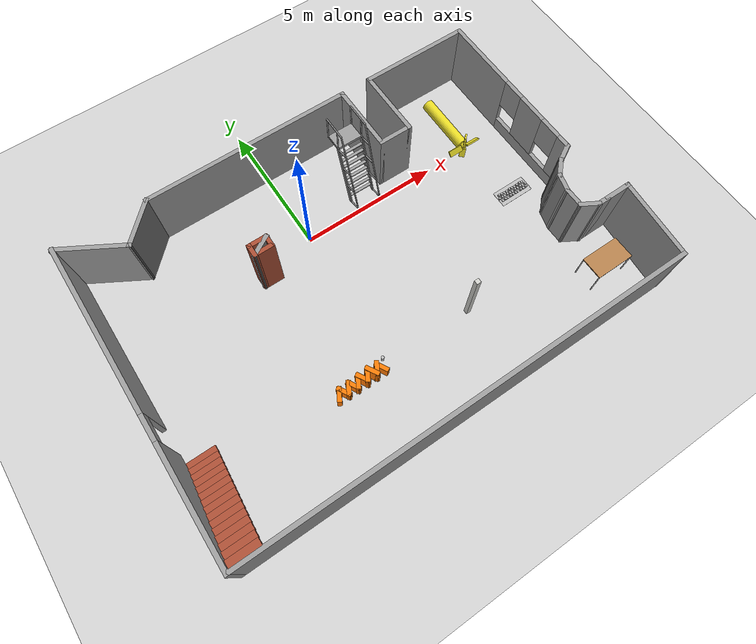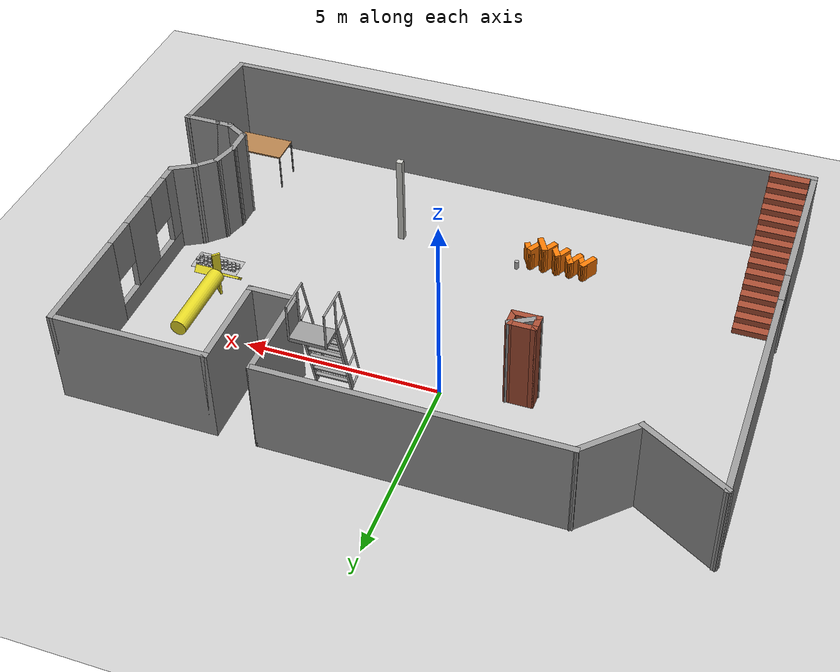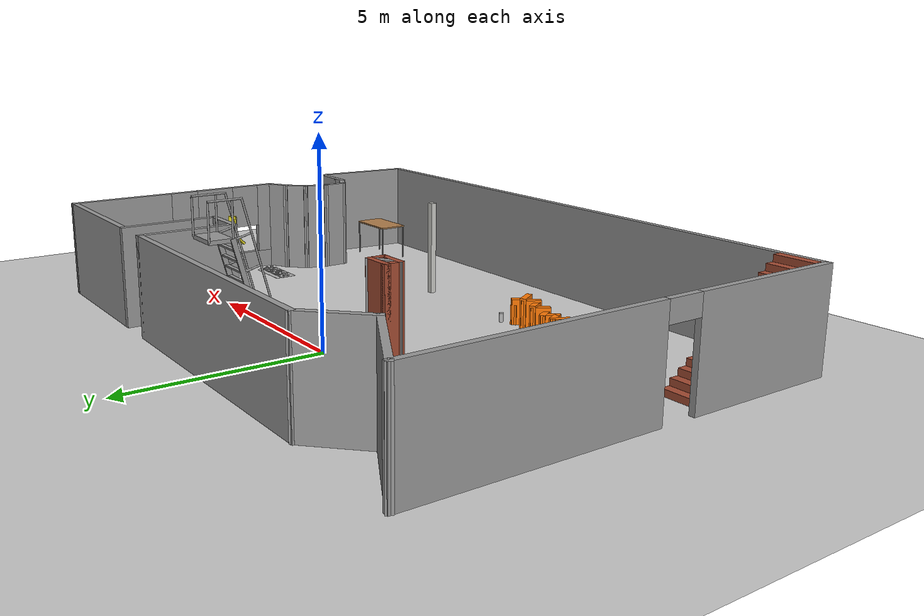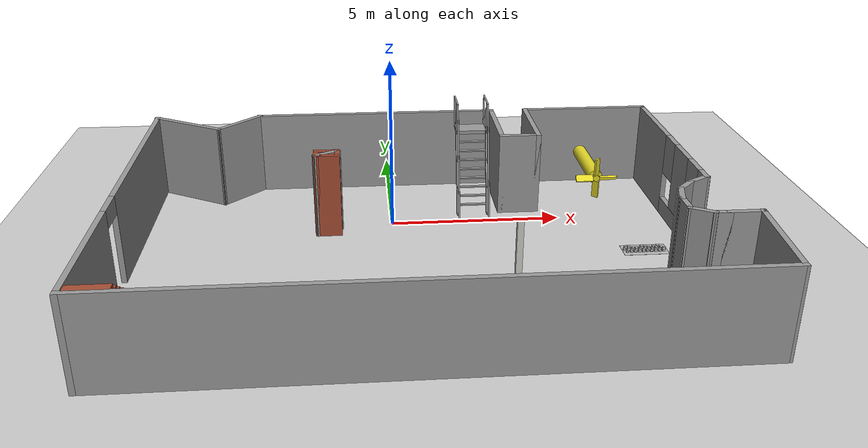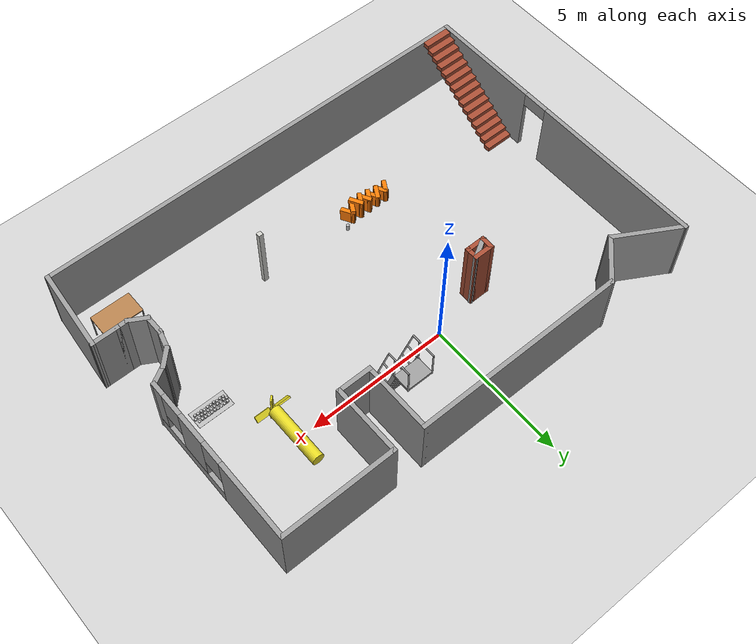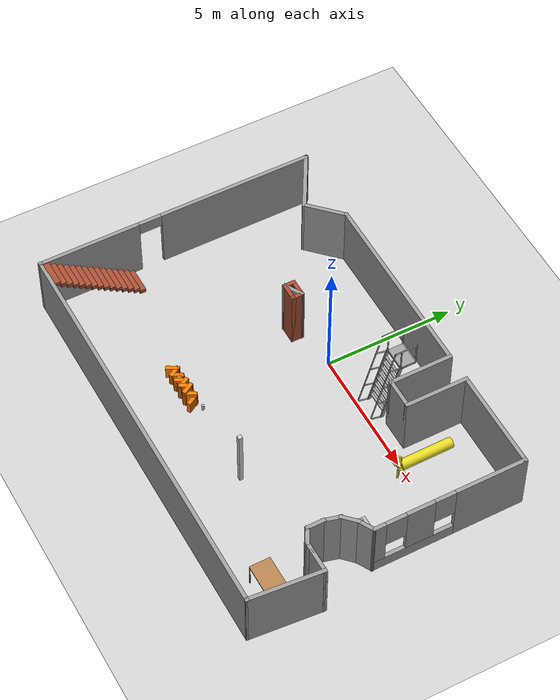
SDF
<sdf version="1.6">
 <world name="default">
  <light name="sun" type="directional">
   <pose>0 0 10 0 -0 0</pose>
   <diffuse>0.8 0.8 0.8 1</diffuse>
   <specular>0.1 0.1 0.1 1</specular>
   <attenuation>
    <range>1000</range>
    <constant>0.9</constant>
    <linear>0.01</linear>
    <quadratic>0.001</quadratic>
   </attenuation>
   <direction>-0.5 0.5 -1</direction>
  </light>
  <model name="ground_plane">
   <static>1</static>
   <link name="link">
    <collision name="collision">
     <geometry><plane><normal>0 0 1</normal><size>100 100</size></plane></geometry>
     <surface><friction><ode><mu>100</mu><mu2>50</mu2></ode></friction></surface>
    </collision>
    <visual name="visual">
     <cast_shadows>0</cast_shadows>
     <geometry><plane><normal>0 0 1</normal><size>100 100</size></plane></geometry>
     <material>
      <script><uri>file://media/materials/scripts/gazebo.material</uri><name>Gazebo/Grey</name></script>
     </material>
    </visual>
   </link>
  </model>
  <gravity>0 0 -9.8</gravity>
  <magnetic_field>6e-06 2.3e-05 -4.2e-05</magnetic_field>
  <atmosphere type="adiabatic"/>
  <physics name="default_physics" default="0" type="ode">
   <max_step_size>0.001</max_step_size>
   <real_time_factor>1</real_time_factor>
   <real_time_update_rate>1000</real_time_update_rate>
  </physics>
  <scene><ambient>0.4 0.4 0.4 1</ambient><background>0.7 0.7 0.7 1</background><shadows>1</shadows></scene>
  <spherical_coordinates>
   <surface_model>EARTH_WGS84</surface_model>
   <latitude_deg>0</latitude_deg>
   <longitude_deg>0</longitude_deg>
   <elevation>0</elevation>
   <heading_deg>0</heading_deg>
  </spherical_coordinates>
  <model name="industria_basica">
   <pose>0.834406 -2.44932 0 0 -0 0</pose>
   <link name="Stairs_0">
    <visual name="Stairs_0_Visual_0">
     <pose>-7.4348 -1.99326 0.083333 0 -0 0</pose>
     <geometry><box><size>1 0.233333 0.166667</size></box></geometry>
     <material>
      <script><uri>file://media/materials/scripts/gazebo.material</uri><name>Gazebo/Bricks</name></script>
      <ambient>1 1 1 1</ambient>
     </material>
    </visual>
    <collision name="Stairs_0_Collision_0">
     <geometry><box><size>1 0.233333 0.166667</size></box></geometry>
     <pose>-7.4348 -1.99326 0.083333 0 -0 0</pose>
    </collision>
    <visual name="Stairs_0_Visual_1">
     <pose>-7.4348 -2.22659 0.25 0 -0 0</pose>
     <geometry><box><size>1 0.233333 0.166667</size></box></geometry>
     <material>
      <script><uri>file://media/materials/scripts/gazebo.material</uri><name>Gazebo/Bricks</name></script>
      <ambient>1 1 1 1</ambient>
     </material>
    </visual>
    <collision name="Stairs_0_Collision_1">
     <geometry><box><size>1 0.233333 0.166667</size></box></geometry>
     <pose>-7.4348 -2.22659 0.25 0 -0 0</pose>
    </collision>
    <visual name="Stairs_0_Visual_2">
     <pose>-7.4348 -2.45992 0.416667 0 -0 0</pose>
     <geometry><box><size>1 0.233333 0.166667</size></box></geometry>
     <material>
      <script><uri>file://media/materials/scripts/gazebo.material</uri><name>Gazebo/Bricks</name></script>
      <ambient>1 1 1 1</ambient>
     </material>
    </visual>
    <collision name="Stairs_0_Collision_2">
     <geometry><box><size>1 0.233333 0.166667</size></box></geometry>
     <pose>-7.4348 -2.45992 0.416667 0 -0 0</pose>
    </collision>
    <visual name="Stairs_0_Visual_3">
     <pose>-7.4348 -2.69326 0.583333 0 -0 0</pose>
     <geometry><box><size>1 0.233333 0.166667</size></box></geometry>
     <material>
      <script><uri>file://media/materials/scripts/gazebo.material</uri><name>Gazebo/Bricks</name></script>
      <ambient>1 1 1 1</ambient>
     </material>
    </visual>
    <collision name="Stairs_0_Collision_3">
     <geometry><box><size>1 0.233333 0.166667</size></box></geometry>
     <pose>-7.4348 -2.69326 0.583333 0 -0 0</pose>
    </collision>
    <visual name="Stairs_0_Visual_4">
     <pose>-7.4348 -2.92659 0.75 0 -0 0</pose>
     <geometry><box><size>1 0.233333 0.166667</size></box></geometry>
     <material>
      <script><uri>file://media/materials/scripts/gazebo.material</uri><name>Gazebo/Bricks</name></script>
      <ambient>1 1 1 1</ambient>
     </material>
    </visual>
    <collision name="Stairs_0_Collision_4">
     <geometry><box><size>1 0.233333 0.166667</size></box></geometry>
     <pose>-7.4348 -2.92659 0.75 0 -0 0</pose>
    </collision>
    <visual name="Stairs_0_Visual_5">
     <pose>-7.4348 -3.15992 0.916667 0 -0 0</pose>
     <geometry><box><size>1 0.233333 0.166667</size></box></geometry>
     <material>
      <script><uri>file://media/materials/scripts/gazebo.material</uri><name>Gazebo/Bricks</name></script>
      <ambient>1 1 1 1</ambient>
     </material>
    </visual>
    <collision name="Stairs_0_Collision_5">
     <geometry><box><size>1 0.233333 0.166667</size></box></geometry>
     <pose>-7.4348 -3.15992 0.916667 0 -0 0</pose>
    </collision>
    <visual name="Stairs_0_Visual_6">
     <pose>-7.4348 -3.39326 1.08333 0 -0 0</pose>
     <geometry><box><size>1 0.233333 0.166667</size></box></geometry>
     <material>
      <script><uri>file://media/materials/scripts/gazebo.material</uri><name>Gazebo/Bricks</name></script>
      <ambient>1 1 1 1</ambient>
     </material>
    </visual>
    <collision name="Stairs_0_Collision_6">
     <geometry><box><size>1 0.233333 0.166667</size></box></geometry>
     <pose>-7.4348 -3.39326 1.08333 0 -0 0</pose>
    </collision>
    <visual name="Stairs_0_Visual_7">
     <pose>-7.4348 -3.62659 1.25 0 -0 0</pose>
     <geometry><box><size>1 0.233333 0.166667</size></box></geometry>
     <material>
      <script><uri>file://media/materials/scripts/gazebo.material</uri><name>Gazebo/Bricks</name></script>
      <ambient>1 1 1 1</ambient>
     </material>
    </visual>
    <collision name="Stairs_0_Collision_7">
     <geometry><box><size>1 0.233333 0.166667</size></box></geometry>
     <pose>-7.4348 -3.62659 1.25 0 -0 0</pose>
    </collision>
    <visual name="Stairs_0_Visual_8">
     <pose>-7.4348 -3.85992 1.41667 0 -0 0</pose>
     <geometry><box><size>1 0.233333 0.166667</size></box></geometry>
     <material>
      <script><uri>file://media/materials/scripts/gazebo.material</uri><name>Gazebo/Bricks</name></script>
      <ambient>1 1 1 1</ambient>
     </material>
    </visual>
    <collision name="Stairs_0_Collision_8">
     <geometry><box><size>1 0.233333 0.166667</size></box></geometry>
     <pose>-7.4348 -3.85992 1.41667 0 -0 0</pose>
    </collision>
    <visual name="Stairs_0_Visual_9">
     <pose>-7.4348 -4.09326 1.58333 0 -0 0</pose>
     <geometry><box><size>1 0.233333 0.166667</size></box></geometry>
     <material>
      <script><uri>file://media/materials/scripts/gazebo.material</uri><name>Gazebo/Bricks</name></script>
      <ambient>1 1 1 1</ambient>
     </material>
    </visual>
    <collision name="Stairs_0_Collision_9">
     <geometry><box><size>1 0.233333 0.166667</size></box></geometry>
     <pose>-7.4348 -4.09326 1.58333 0 -0 0</pose>
    </collision>
    <visual name="Stairs_0_Visual_10">
     <pose>-7.4348 -4.32659 1.75 0 -0 0</pose>
     <geometry><box><size>1 0.233333 0.166667</size></box></geometry>
     <material>
      <script><uri>file://media/materials/scripts/gazebo.material</uri><name>Gazebo/Bricks</name></script>
      <ambient>1 1 1 1</ambient>
     </material>
    </visual>
    <collision name="Stairs_0_Collision_10">
     <geometry><box><size>1 0.233333 0.166667</size></box></geometry>
     <pose>-7.4348 -4.32659 1.75 0 -0 0</pose>
    </collision>
    <visual name="Stairs_0_Visual_11">
     <pose>-7.4348 -4.55992 1.91667 0 -0 0</pose>
     <geometry><box><size>1 0.233333 0.166667</size></box></geometry>
     <material>
      <script><uri>file://media/materials/scripts/gazebo.material</uri><name>Gazebo/Bricks</name></script>
      <ambient>1 1 1 1</ambient>
     </material>
    </visual>
    <collision name="Stairs_0_Collision_11">
     <geometry><box><size>1 0.233333 0.166667</size></box></geometry>
     <pose>-7.4348 -4.55992 1.91667 0 -0 0</pose>
    </collision>
    <visual name="Stairs_0_Visual_12">
     <pose>-7.4348 -4.79326 2.08333 0 -0 0</pose>
     <geometry><box><size>1 0.233333 0.166667</size></box></geometry>
     <material>
      <script><uri>file://media/materials/scripts/gazebo.material</uri><name>Gazebo/Bricks</name></script>
      <ambient>1 1 1 1</ambient>
     </material>
    </visual>
    <collision name="Stairs_0_Collision_12">
     <geometry><box><size>1 0.233333 0.166667</size></box></geometry>
     <pose>-7.4348 -4.79326 2.08333 0 -0 0</pose>
    </collision>
    <visual name="Stairs_0_Visual_13">
     <pose>-7.4348 -5.02659 2.25 0 -0 0</pose>
     <geometry><box><size>1 0.233333 0.166667</size></box></geometry>
     <material>
      <script><uri>file://media/materials/scripts/gazebo.material</uri><name>Gazebo/Bricks</name></script>
      <ambient>1 1 1 1</ambient>
     </material>
    </visual>
    <collision name="Stairs_0_Collision_13">
     <geometry><box><size>1 0.233333 0.166667</size></box></geometry>
     <pose>-7.4348 -5.02659 2.25 0 -0 0</pose>
    </collision>
    <visual name="Stairs_0_Visual_14">
     <pose>-7.4348 -5.25992 2.41667 0 -0 0</pose>
     <geometry><box><size>1 0.233333 0.166667</size></box></geometry>
     <material>
      <script><uri>file://media/materials/scripts/gazebo.material</uri><name>Gazebo/Bricks</name></script>
      <ambient>1 1 1 1</ambient>
     </material>
    </visual>
    <collision name="Stairs_0_Collision_14">
     <geometry><box><size>1 0.233333 0.166667</size></box></geometry>
     <pose>-7.4348 -5.25992 2.41667 0 -0 0</pose>
    </collision>
   </link>
   <link name="Wall_10">
    <collision name="Wall_10_Collision">
     <geometry><box><size>7.5 0.15 2.5</size></box></geometry>
     <pose>0 0 1.25 0 -0 0</pose>
    </collision>
    <visual name="Wall_10_Visual">
     <pose>0 0 1.25 0 -0 0</pose>
     <geometry><box><size>7.5 0.15 2.5</size></box></geometry>
     <material>
      <script><uri>file://media/materials/scripts/gazebo.material</uri><name>Gazebo/Grey</name></script>
      <ambient>1 1 1 1</ambient>
     </material>
    </visual>
    <pose>-1.19131 5.37072 0 0 -0 0</pose>
   </link>
   <link name="Wall_11">
    <collision name="Wall_11_Collision">
     <geometry><box><size>2.5 0.15 2.5</size></box></geometry>
     <pose>0 0 1.25 0 -0 0</pose>
    </collision>
    <visual name="Wall_11_Visual">
     <pose>0 0 1.25 0 -0 0</pose>
     <geometry><box><size>2.5 0.15 2.5</size></box></geometry>
     <material>
      <script><uri>file://media/materials/scripts/gazebo.material</uri><name>Gazebo/Grey</name></script>
      <ambient>1 1 1 1</ambient>
     </material>
    </visual>
    <pose>2.48369 4.19572 0 0 0 -1.5708</pose>
   </link>
   <link name="Wall_12">
    <collision name="Wall_12_Collision">
     <geometry><box><size>1.25 0.15 2.5</size></box></geometry>
     <pose>0 0 1.25 0 -0 0</pose>
    </collision>
    <visual name="Wall_12_Visual">
     <pose>0 0 1.25 0 -0 0</pose>
     <geometry><box><size>1.25 0.15 2.5</size></box></geometry>
     <material>
      <script><uri>file://media/materials/scripts/gazebo.material</uri><name>Gazebo/Grey</name></script>
      <ambient>1 1 1 1</ambient>
     </material>
    </visual>
    <pose>3.03369 3.02072 0 0 -0 0</pose>
   </link>
   <link name="Wall_13">
    <collision name="Wall_13_Collision">
     <geometry><box><size>2.5 0.15 2.5</size></box></geometry>
     <pose>0 0 1.25 0 -0 0</pose>
    </collision>
    <visual name="Wall_13_Visual">
     <pose>0 0 1.25 0 -0 0</pose>
     <geometry><box><size>2.5 0.15 2.5</size></box></geometry>
     <material>
      <script><uri>file://media/materials/scripts/gazebo.material</uri><name>Gazebo/Grey</name></script>
      <ambient>1 1 1 1</ambient>
     </material>
    </visual>
    <pose>3.58369 4.19572 0 0 -0 1.5708</pose>
   </link>
   <link name="Wall_14">
    <collision name="Wall_14_Collision">
     <geometry><box><size>4 0.15 2.5</size></box></geometry>
     <pose>0 0 1.25 0 -0 0</pose>
    </collision>
    <visual name="Wall_14_Visual">
     <pose>0 0 1.25 0 -0 0</pose>
     <geometry><box><size>4 0.15 2.5</size></box></geometry>
     <material>
      <script><uri>file://media/materials/scripts/gazebo.material</uri><name>Gazebo/Grey</name></script>
      <ambient>1 1 1 1</ambient>
     </material>
    </visual>
    <pose>5.50869 5.37072 0 0 -0 0</pose>
   </link>
   <link name="Wall_15">
    <pose>7.43369 2.44572 0 0 0 -1.5708</pose>
    <visual name="Wall_15_Visual_0">
     <pose>-1.60274 0 1.25 0 -0 0</pose>
     <geometry><box><size>2.79452 0.15 2.5</size></box></geometry>
     <material>
      <script><uri>file://media/materials/scripts/gazebo.material</uri><name>Gazebo/Grey</name></script>
      <ambient>1 1 1 1</ambient>
     </material>
    </visual>
    <collision name="Wall_15_Collision_0">
     <geometry><box><size>2.79452 0.15 2.5</size></box></geometry>
     <pose>-1.60274 0 1.25 0 -0 0</pose>
    </collision>
    <visual name="Wall_15_Visual_1">
     <pose>1.39726 0 0.25 0 -0 0</pose>
     <geometry><box><size>3.20548 0.15 0.5</size></box></geometry>
     <material>
      <script><uri>file://media/materials/scripts/gazebo.material</uri><name>Gazebo/Grey</name></script>
      <ambient>1 1 1 1</ambient>
     </material>
    </visual>
    <collision name="Wall_15_Collision_1">
     <geometry><box><size>3.20548 0.15 0.5</size></box></geometry>
     <pose>1.39726 0 0.25 0 -0 0</pose>
    </collision>
    <visual name="Wall_15_Visual_2">
     <pose>1.13916 0 1.5 0 -0 0</pose>
     <geometry><box><size>1.08927 0.15 2</size></box></geometry>
     <material>
      <script><uri>file://media/materials/scripts/gazebo.material</uri><name>Gazebo/Grey</name></script>
      <ambient>1 1 1 1</ambient>
     </material>
    </visual>
    <collision name="Wall_15_Collision_2">
     <geometry><box><size>1.08927 0.15 2</size></box></geometry>
     <pose>1.13916 0 1.5 0 -0 0</pose>
    </collision>
    <visual name="Wall_15_Visual_3">
     <pose>2.7419 0 1.5 0 -0 0</pose>
     <geometry><box><size>0.516207 0.15 2</size></box></geometry>
     <material>
      <script><uri>file://media/materials/scripts/gazebo.material</uri><name>Gazebo/Grey</name></script>
      <ambient>1 1 1 1</ambient>
     </material>
    </visual>
    <collision name="Wall_15_Collision_3">
     <geometry><box><size>0.516207 0.15 2</size></box></geometry>
     <pose>2.7419 0 1.5 0 -0 0</pose>
    </collision>
    <visual name="Wall_15_Visual_4">
     <pose>0.194521 0 1.9 0 -0 0</pose>
     <geometry><box><size>0.8 0.15 1.2</size></box></geometry>
     <material>
      <script><uri>file://media/materials/scripts/gazebo.material</uri><name>Gazebo/Grey</name></script>
      <ambient>1 1 1 1</ambient>
     </material>
    </visual>
    <collision name="Wall_15_Collision_4">
     <geometry><box><size>0.8 0.15 1.2</size></box></geometry>
     <pose>0.194521 0 1.9 0 -0 0</pose>
    </collision>
    <visual name="Wall_15_Visual_5">
     <pose>2.08379 0 1.9 0 -0 0</pose>
     <geometry><box><size>0.8 0.15 1.2</size></box></geometry>
     <material>
      <script><uri>file://media/materials/scripts/gazebo.material</uri><name>Gazebo/Grey</name></script>
      <ambient>1 1 1 1</ambient>
     </material>
    </visual>
    <collision name="Wall_15_Collision_5">
     <geometry><box><size>0.8 0.15 1.2</size></box></geometry>
     <pose>2.08379 0 1.9 0 -0 0</pose>
    </collision>
   </link>
   <link name="Wall_16">
    <collision name="Wall_16_Collision">
     <geometry><box><size>0.75 0.15 2.5</size></box></geometry>
     <pose>0 0 1.25 0 -0 0</pose>
    </collision>
    <visual name="Wall_16_Visual">
     <pose>0 0 1.25 0 -0 0</pose>
     <geometry><box><size>0.75 0.15 2.5</size></box></geometry>
     <material>
      <script><uri>file://media/materials/scripts/gazebo.material</uri><name>Gazebo/Grey</name></script>
      <ambient>1 1 1 1</ambient>
     </material>
    </visual>
    <pose>7.17388 -0.629277 0 0 0 -2.61799</pose>
   </link>
   <link name="Wall_17">
    <collision name="Wall_17_Collision">
     <geometry><box><size>0.75 0.15 2.5</size></box></geometry>
     <pose>0 0 1.25 0 -0 0</pose>
    </collision>
    <visual name="Wall_17_Visual">
     <pose>0 0 1.25 0 -0 0</pose>
     <geometry><box><size>0.75 0.15 2.5</size></box></geometry>
     <material>
      <script><uri>file://media/materials/scripts/gazebo.material</uri><name>Gazebo/Grey</name></script>
      <ambient>1 1 1 1</ambient>
     </material>
    </visual>
    <pose>6.70194 -0.991409 0 0 0 -2.35619</pose>
   </link>
   <link name="Wall_18">
    <collision name="Wall_18_Collision">
     <geometry><box><size>0.75 0.15 2.5</size></box></geometry>
     <pose>0 0 1.25 0 -0 0</pose>
    </collision>
    <visual name="Wall_18_Visual">
     <pose>0 0 1.25 0 -0 0</pose>
     <geometry><box><size>0.75 0.15 2.5</size></box></geometry>
     <material>
      <script><uri>file://media/materials/scripts/gazebo.material</uri><name>Gazebo/Grey</name></script>
      <ambient>1 1 1 1</ambient>
     </material>
    </visual>
    <pose>6.41217 -1.49332 0 0 0 -1.8326</pose>
   </link>
   <link name="Wall_19">
    <collision name="Wall_19_Collision">
     <geometry><box><size>0.75 0.15 2.5</size></box></geometry>
     <pose>0 0 1.25 0 -0 0</pose>
    </collision>
    <visual name="Wall_19_Visual">
     <pose>0 0 1.25 0 -0 0</pose>
     <geometry><box><size>0.75 0.15 2.5</size></box></geometry>
     <material>
      <script><uri>file://media/materials/scripts/gazebo.material</uri><name>Gazebo/Grey</name></script>
      <ambient>1 1 1 1</ambient>
     </material>
    </visual>
    <pose>6.33452 -2.0831 0 0 0 -1.5708</pose>
   </link>
   <link name="Wall_20">
    <collision name="Wall_20_Collision">
     <geometry><box><size>0.75 0.15 2.5</size></box></geometry>
     <pose>0 0 1.25 0 -0 0</pose>
    </collision>
    <visual name="Wall_20_Visual">
     <pose>0 0 1.25 0 -0 0</pose>
     <geometry><box><size>0.75 0.15 2.5</size></box></geometry>
     <material>
      <script><uri>file://media/materials/scripts/gazebo.material</uri><name>Gazebo/Grey</name></script>
      <ambient>1 1 1 1</ambient>
     </material>
    </visual>
    <pose>6.59433 -2.5331 0 0 0 -0.523599</pose>
   </link>
   <link name="Wall_21">
    <collision name="Wall_21_Collision">
     <geometry><box><size>0.5 0.15 2.5</size></box></geometry>
     <pose>0 0 1.25 0 -0 0</pose>
    </collision>
    <visual name="Wall_21_Visual">
     <pose>0 0 1.25 0 -0 0</pose>
     <geometry><box><size>0.5 0.15 2.5</size></box></geometry>
     <material>
      <script><uri>file://media/materials/scripts/gazebo.material</uri><name>Gazebo/Grey</name></script>
      <ambient>1 1 1 1</ambient>
     </material>
    </visual>
    <pose>7.02914 -2.6831 0 0 -0 0</pose>
   </link>
   <link name="Wall_22">
    <collision name="Wall_22_Collision">
     <geometry><box><size>1 0.15 2.5</size></box></geometry>
     <pose>0 0 1.25 0 -0 0</pose>
    </collision>
    <visual name="Wall_22_Visual">
     <pose>0 0 1.25 0 -0 0</pose>
     <geometry><box><size>1 0.15 2.5</size></box></geometry>
     <material>
      <script><uri>file://media/materials/scripts/gazebo.material</uri><name>Gazebo/Grey</name></script>
      <ambient>1 1 1 1</ambient>
     </material>
    </visual>
    <pose>7.62913 -2.6831 0 0 -0 0</pose>
   </link>
   <link name="Wall_23">
    <collision name="Wall_23_Collision">
     <geometry><box><size>2.91273 0.15 2.5</size></box></geometry>
     <pose>0 0 1.25 0 -0 0</pose>
    </collision>
    <visual name="Wall_23_Visual">
     <pose>0 0 1.25 0 -0 0</pose>
     <geometry><box><size>2.91273 0.15 2.5</size></box></geometry>
     <material>
      <script><uri>file://media/materials/scripts/gazebo.material</uri><name>Gazebo/Grey</name></script>
      <ambient>1 1 1 1</ambient>
     </material>
    </visual>
    <pose>7.93565 -4.05937 0 0 0 -1.65668</pose>
   </link>
   <link name="Wall_4">
    <pose>-8.03284 -0.010648 0 0 0 -1.5708</pose>
    <visual name="Wall_4_Visual_0">
     <pose>-2.45105 0 1.25 0 -0 0</pose>
     <geometry><box><size>6.09789 0.15 2.5</size></box></geometry>
     <material>
      <script><uri>file://media/materials/scripts/gazebo.material</uri><name>Gazebo/Grey</name></script>
      <ambient>1 1 1 1</ambient>
     </material>
    </visual>
    <collision name="Wall_4_Collision_0">
     <geometry><box><size>6.09789 0.15 2.5</size></box></geometry>
     <pose>-2.45105 0 1.25 0 -0 0</pose>
    </collision>
    <visual name="Wall_4_Visual_1">
     <pose>3.49895 0 1.25 0 -0 0</pose>
     <geometry><box><size>4.00211 0.15 2.5</size></box></geometry>
     <material>
      <script><uri>file://media/materials/scripts/gazebo.material</uri><name>Gazebo/Grey</name></script>
      <ambient>1 1 1 1</ambient>
     </material>
    </visual>
    <collision name="Wall_4_Collision_1">
     <geometry><box><size>4.00211 0.15 2.5</size></box></geometry>
     <pose>3.49895 0 1.25 0 -0 0</pose>
    </collision>
    <visual name="Wall_4_Visual_2">
     <pose>1.04789 0 2.25 0 -0 0</pose>
     <geometry><box><size>0.9 0.15 0.5</size></box></geometry>
     <material>
      <script><uri>file://media/materials/scripts/gazebo.material</uri><name>Gazebo/Grey</name></script>
      <ambient>1 1 1 1</ambient>
     </material>
    </visual>
    <collision name="Wall_4_Collision_2">
     <geometry><box><size>0.9 0.15 0.5</size></box></geometry>
     <pose>1.04789 0 2.25 0 -0 0</pose>
    </collision>
   </link>
   <link name="Wall_5">
    <collision name="Wall_5_Collision">
     <geometry><box><size>16 0.15 2.5</size></box></geometry>
     <pose>0 0 1.25 0 -0 0</pose>
    </collision>
    <visual name="Wall_5_Visual">
     <pose>0 0 1.25 0 -0 0</pose>
     <geometry><box><size>16 0.15 2.5</size></box></geometry>
     <material>
      <script><uri>file://media/materials/scripts/gazebo.material</uri><name>Gazebo/Grey</name></script>
      <ambient>1 1 1 1</ambient>
     </material>
    </visual>
    <pose>-0.10784 -5.43565 0 0 -0 0</pose>
   </link>
   <link name="Wall_8">
    <collision name="Wall_8_Collision">
     <geometry><box><size>2.5 0.15 2.5</size></box></geometry>
     <pose>0 0 1.25 0 -0 0</pose>
    </collision>
    <visual name="Wall_8_Visual">
     <pose>0 0 1.25 0 -0 0</pose>
     <geometry><box><size>2.5 0.15 2.5</size></box></geometry>
     <material>
      <script><uri>file://media/materials/scripts/gazebo.material</uri><name>Gazebo/Grey</name></script>
      <ambient>1 1 1 1</ambient>
     </material>
    </visual>
    <pose>-7.01526 4.82685 0 0 0 -0.523599</pose>
   </link>
   <link name="Wall_9">
    <collision name="Wall_9_Collision">
     <geometry><box><size>1.75 0.15 2.5</size></box></geometry>
     <pose>0 0 1.25 0 -0 0</pose>
    </collision>
    <visual name="Wall_9_Visual">
     <pose>0 0 1.25 0 -0 0</pose>
     <geometry><box><size>1.75 0.15 2.5</size></box></geometry>
     <material>
      <script><uri>file://media/materials/scripts/gazebo.material</uri><name>Gazebo/Grey</name></script>
      <ambient>1 1 1 1</ambient>
     </material>
    </visual>
    <pose>-5.43199 4.80504 0 0 -0 0.785398</pose>
   </link>
   <static>1</static>
  </model>
  <model name="industria_basica2">
   <pose>0.305179 -2.81957 0 0 -0 0</pose>
   <link name="Wall_1">
    <collision name="Wall_1_Collision">
     <geometry><box><size>0.16 0.15 2.5</size></box></geometry>
     <pose>0 0 1.25 0 -0 0</pose>
    </collision>
    <visual name="Wall_1_Visual">
     <pose>0 0 1.25 0 -0 0</pose>
     <geometry><box><size>0.16 0.15 2.5</size></box></geometry>
     <material>
      <script><uri>file://media/materials/scripts/gazebo.material</uri><name>Gazebo/CeilingTiled</name></script>
      <ambient>1 1 1 1</ambient>
     </material>
    </visual>
    <pose>2.58924 -2.29315 0 0 -0 0</pose>
   </link>
   <link name="Wall_10">
    <collision name="Wall_10_Collision">
     <geometry><box><size>0.844622 0.15 2.5</size></box></geometry>
     <pose>0 0 1.25 0 -0 0</pose>
    </collision>
    <visual name="Wall_10_Visual">
     <pose>0 0 1.25 0 -0 0</pose>
     <geometry><box><size>0.844622 0.15 2.5</size></box></geometry>
     <material>
      <script><uri>file://media/materials/scripts/gazebo.material</uri><name>Gazebo/Grey</name></script>
      <ambient>1 1 1 1</ambient>
     </material>
    </visual>
    <pose>-2.16698 2.35707 0 0 0 -2.61352</pose>
   </link>
   <link name="Wall_21">
    <collision name="Wall_21_Collision">
     <geometry><box><size>0.5 0.15 0.5</size></box></geometry>
     <pose>0 0 0.25 0 -0 0</pose>
    </collision>
    <visual name="Wall_21_Visual">
     <pose>0 0 0.25 0 -0 0</pose>
     <geometry><box><size>0.5 0.15 0.5</size></box></geometry>
     <material>
      <script><uri>file://media/materials/scripts/gazebo.material</uri><name>Gazebo/Grey</name></script>
      <ambient>0.996078 0.47451 0.0196078 1</ambient>
     </material>
    </visual>
    <pose>-2.47926 -2.38065 0 0 -0 1.04704</pose>
   </link>
   <link name="Wall_22">
    <collision name="Wall_22_Collision">
     <geometry><box><size>0.5 0.15 0.5</size></box></geometry>
     <pose>0 0 0.25 0 -0 0</pose>
    </collision>
    <visual name="Wall_22_Visual">
     <pose>0 0 0.25 0 -0 0</pose>
     <geometry><box><size>0.5 0.15 0.5</size></box></geometry>
     <material>
      <script><uri>file://media/materials/scripts/gazebo.material</uri><name>Gazebo/Grey</name></script>
      <ambient>0.996078 0.47451 0.0196078 1</ambient>
     </material>
    </visual>
    <pose>-2.30426 -2.38065 0 0 0 -1.04704</pose>
   </link>
   <link name="Wall_23">
    <collision name="Wall_23_Collision">
     <geometry><box><size>0.5 0.15 0.5</size></box></geometry>
     <pose>0 0 0.25 0 -0 0</pose>
    </collision>
    <visual name="Wall_23_Visual">
     <pose>0 0 0.25 0 -0 0</pose>
     <geometry><box><size>0.5 0.15 0.5</size></box></geometry>
     <material>
      <script><uri>file://media/materials/scripts/gazebo.material</uri><name>Gazebo/Grey</name></script>
      <ambient>0.996078 0.47451 0.0196078 1</ambient>
     </material>
    </visual>
    <pose>-2.12926 -2.38065 0 0 -0 1.04704</pose>
   </link>
   <link name="Wall_24">
    <collision name="Wall_24_Collision">
     <geometry><box><size>0.5 0.15 0.5</size></box></geometry>
     <pose>0 0 0.25 0 -0 0</pose>
    </collision>
    <visual name="Wall_24_Visual">
     <pose>0 0 0.25 0 -0 0</pose>
     <geometry><box><size>0.5 0.15 0.5</size></box></geometry>
     <material>
      <script><uri>file://media/materials/scripts/gazebo.material</uri><name>Gazebo/Grey</name></script>
      <ambient>0.996078 0.47451 0.0196078 1</ambient>
     </material>
    </visual>
    <pose>-1.95426 -2.38065 0 0 0 -1.04704</pose>
   </link>
   <link name="Wall_25">
    <collision name="Wall_25_Collision">
     <geometry><box><size>0.5 0.15 0.6</size></box></geometry>
     <pose>0 0 0.3 0 -0 0</pose>
    </collision>
    <visual name="Wall_25_Visual">
     <pose>0 0 0.3 0 -0 0</pose>
     <geometry><box><size>0.5 0.15 0.6</size></box></geometry>
     <material>
      <script><uri>file://media/materials/scripts/gazebo.material</uri><name>Gazebo/Grey</name></script>
      <ambient>0.996078 0.47451 0.0196078 1</ambient>
     </material>
    </visual>
    <pose>-1.77926 -2.38065 0 0 -0 1.04704</pose>
   </link>
   <link name="Wall_26">
    <collision name="Wall_26_Collision">
     <geometry><box><size>0.5 0.15 0.65</size></box></geometry>
     <pose>0 0 0.325 0 -0 0</pose>
    </collision>
    <visual name="Wall_26_Visual">
     <pose>0 0 0.325 0 -0 0</pose>
     <geometry><box><size>0.5 0.15 0.65</size></box></geometry>
     <material>
      <script><uri>file://media/materials/scripts/gazebo.material</uri><name>Gazebo/Grey</name></script>
      <ambient>0.996078 0.47451 0.0196078 1</ambient>
     </material>
    </visual>
    <pose>-1.60426 -2.38065 0 0 0 -1.04704</pose>
   </link>
   <link name="Wall_27">
    <collision name="Wall_27_Collision">
     <geometry><box><size>0.5 0.15 0.7</size></box></geometry>
     <pose>0 0 0.35 0 -0 0</pose>
    </collision>
    <visual name="Wall_27_Visual">
     <pose>0 0 0.35 0 -0 0</pose>
     <geometry><box><size>0.5 0.15 0.7</size></box></geometry>
     <material>
      <script><uri>file://media/materials/scripts/gazebo.material</uri><name>Gazebo/Grey</name></script>
      <ambient>0.996078 0.47451 0.0196078 1</ambient>
     </material>
    </visual>
    <pose>-1.42926 -2.38065 0 0 -0 1.04704</pose>
   </link>
   <link name="Wall_28">
    <collision name="Wall_28_Collision">
     <geometry><box><size>0.5 0.15 0.75</size></box></geometry>
     <pose>0 0 0.375 0 -0 0</pose>
    </collision>
    <visual name="Wall_28_Visual">
     <pose>0 0 0.375 0 -0 0</pose>
     <geometry><box><size>0.5 0.15 0.75</size></box></geometry>
     <material>
      <script><uri>file://media/materials/scripts/gazebo.material</uri><name>Gazebo/Grey</name></script>
      <ambient>0.996078 0.47451 0.0196078 1</ambient>
     </material>
    </visual>
    <pose>-1.25426 -2.38065 0 0 0 -1.04704</pose>
   </link>
   <link name="Wall_29">
    <collision name="Wall_29_Collision">
     <geometry><box><size>0.5 0.15 0.65</size></box></geometry>
     <pose>0 0 0.325 0 -0 0</pose>
    </collision>
    <visual name="Wall_29_Visual">
     <pose>0 0 0.325 0 -0 0</pose>
     <geometry><box><size>0.5 0.15 0.65</size></box></geometry>
     <material>
      <script><uri>file://media/materials/scripts/gazebo.material</uri><name>Gazebo/Grey</name></script>
      <ambient>0.996078 0.47451 0.0196078 1</ambient>
     </material>
    </visual>
    <pose>-1.07926 -2.38065 0 0 -0 1.04704</pose>
   </link>
   <link name="Wall_30">
    <collision name="Wall_30_Collision">
     <geometry><box><size>0.5 0.15 0.5</size></box></geometry>
     <pose>0 0 0.25 0 -0 0</pose>
    </collision>
    <visual name="Wall_30_Visual">
     <pose>0 0 0.25 0 -0 0</pose>
     <geometry><box><size>0.5 0.15 0.5</size></box></geometry>
     <material>
      <script><uri>file://media/materials/scripts/gazebo.material</uri><name>Gazebo/Grey</name></script>
      <ambient>0.996078 0.47451 0.0196078 1</ambient>
     </material>
    </visual>
    <pose>-0.90426 -2.38065 0 0 0 -1.04704</pose>
   </link>
   <link name="Wall_6">
    <collision name="Wall_6_Collision">
     <geometry><box><size>0.5 0.15 2.5</size></box></geometry>
     <pose>0 0 1.25 0 -0 0</pose>
    </collision>
    <visual name="Wall_6_Visual">
     <pose>0 0 1.25 0 -0 0</pose>
     <geometry><box><size>0.5 0.15 2.5</size></box></geometry>
     <material>
      <script><uri>file://media/materials/scripts/gazebo.material</uri><name>Gazebo/Bricks</name></script>
      <ambient>1 1 1 1</ambient>
     </material>
    </visual>
    <pose>-1.86698 2.35707 0 0 0 -1.5708</pose>
   </link>
   <link name="Wall_7">
    <collision name="Wall_7_Collision">
     <geometry><box><size>0.75 0.15 2.5</size></box></geometry>
     <pose>0 0 1.25 0 -0 0</pose>
    </collision>
    <visual name="Wall_7_Visual">
     <pose>0 0 1.25 0 -0 0</pose>
     <geometry><box><size>0.75 0.15 2.5</size></box></geometry>
     <material>
      <script><uri>file://media/materials/scripts/gazebo.material</uri><name>Gazebo/Bricks</name></script>
      <ambient>1 1 1 1</ambient>
     </material>
    </visual>
    <pose>-2.16698 2.18207 0 0 -0 3.14159</pose>
   </link>
   <link name="Wall_8">
    <collision name="Wall_8_Collision">
     <geometry><box><size>0.5 0.15 2.5</size></box></geometry>
     <pose>0 0 1.25 0 -0 0</pose>
    </collision>
    <visual name="Wall_8_Visual">
     <pose>0 0 1.25 0 -0 0</pose>
     <geometry><box><size>0.5 0.15 2.5</size></box></geometry>
     <material>
      <script><uri>file://media/materials/scripts/gazebo.material</uri><name>Gazebo/Bricks</name></script>
      <ambient>1 1 1 1</ambient>
     </material>
    </visual>
    <pose>-2.46698 2.35707 0 0 -0 1.5708</pose>
   </link>
   <link name="Wall_9">
    <collision name="Wall_9_Collision">
     <geometry><box><size>0.75 0.15 2.5</size></box></geometry>
     <pose>0 0 1.25 0 -0 0</pose>
    </collision>
    <visual name="Wall_9_Visual">
     <pose>0 0 1.25 0 -0 0</pose>
     <geometry><box><size>0.75 0.15 2.5</size></box></geometry>
     <material>
      <script><uri>file://media/materials/scripts/gazebo.material</uri><name>Gazebo/Bricks</name></script>
      <ambient>1 1 1 1</ambient>
     </material>
    </visual>
    <pose>-2.16698 2.53207 0 0 -0 0</pose>
   </link>
   <static>1</static>
  </model>
  <model name="table">
   <static>0</static>
   <link name="link">
    <collision name="surface">
     <pose>0 0 1 0 -0 0</pose>
     <geometry><box><size>1.5 0.8 0.03</size></box></geometry>
     <surface><friction><ode><mu>0.6</mu><mu2>0.6</mu2></ode></friction></surface>
    </collision>
    <visual name="visual1">
     <pose>0 0 1 0 -0 0</pose>
     <geometry><box><size>1.4 0.8 0.04</size></box></geometry>
     <material>
      <script><uri>file://media/materials/scripts/gazebo.material</uri><name>Gazebo/Wood</name></script>
     </material>
    </visual>
    <collision name="front_left_leg">
     <pose>0.68 0.38 0.5 0 -0 0</pose>
     <geometry><cylinder><radius>0.02</radius><length>1</length></cylinder></geometry>
    </collision>
    <visual name="front_left_leg">
     <pose>0.68 0.38 0.5 0 -0 0</pose>
     <geometry><cylinder><radius>0.02</radius><length>1</length></cylinder></geometry>
     <material>
      <script><uri>file://media/materials/scripts/gazebo.material</uri><name>Gazebo/Grey</name></script>
     </material>
    </visual>
    <collision name="front_right_leg">
     <pose>0.68 -0.38 0.5 0 -0 0</pose>
     <geometry><cylinder><radius>0.02</radius><length>1</length></cylinder></geometry>
    </collision>
    <visual name="front_right_leg">
     <pose>0.68 -0.38 0.5 0 -0 0</pose>
     <geometry><cylinder><radius>0.02</radius><length>1</length></cylinder></geometry>
     <material>
      <script><uri>file://media/materials/scripts/gazebo.material</uri><name>Gazebo/Grey</name></script>
     </material>
    </visual>
    <collision name="back_right_leg">
     <pose>-0.68 -0.38 0.5 0 -0 0</pose>
     <geometry><cylinder><radius>0.02</radius><length>1</length></cylinder></geometry>
    </collision>
    <visual name="back_right_leg">
     <pose>-0.68 -0.38 0.5 0 -0 0</pose>
     <geometry><cylinder><radius>0.02</radius><length>1</length></cylinder></geometry>
     <material>
      <script><uri>file://media/materials/scripts/gazebo.material</uri><name>Gazebo/Grey</name></script>
     </material>
    </visual>
    <collision name="back_left_leg">
     <pose>-0.68 0.38 0.5 0 -0 0</pose>
     <geometry><cylinder><radius>0.02</radius><length>1</length></cylinder></geometry>
    </collision>
    <visual name="back_left_leg">
     <pose>-0.68 0.38 0.5 0 -0 0</pose>
     <geometry><cylinder><radius>0.02</radius><length>1</length></cylinder></geometry>
     <material>
      <script><uri>file://media/materials/scripts/gazebo.material</uri><name>Gazebo/Grey</name></script>
     </material>
    </visual>
    <inertial>
     <inertia><ixx>1</ixx><ixy>0</ixy><ixz>0</ixz><iyy>1</iyy><iyz>0</iyz><izz>1</izz></inertia>
     <mass>1</mass>
    </inertial>
   </link>
   <pose>7.47952 -6.43159 -1e-06 1e-06 -0 0</pose>
  </model>
  <model name="ladder_75deg_2rails">
   <static>1</static>
   <link name="step0">
    <pose>0 0.071453 0.266667 0 -0 0</pose>
    <inertial>
     <mass>9.75482</mass>
     <inertia>
      <ixx>0.00957124</ixx>
      <iyy>0.65963</iyy>
      <izz>0.666842</izz>
      <ixy>0</ixy>
      <ixz>0</ixz>
      <iyz>0</iyz>
     </inertia>
    </inertial>
    <collision name="collision"><geometry><box><size>0.9 0.1016 0.0381</size></box></geometry></collision>
    <visual name="visual">
     <geometry><box><size>0.9 0.1016 0.0381</size></box></geometry>
     <material>
      <script><uri>file://media/materials/scripts/gazebo.material</uri><name>Gazebo/Grey</name></script>
     </material>
    </visual>
   </link>
   <link name="step1">
    <pose>0 0.142906 0.533333 0 -0 0</pose>
    <inertial>
     <mass>9.75482</mass>
     <inertia>
      <ixx>0.00957124</ixx>
      <iyy>0.65963</iyy>
      <izz>0.666842</izz>
      <ixy>0</ixy>
      <ixz>0</ixz>
      <iyz>0</iyz>
     </inertia>
    </inertial>
    <collision name="collision"><geometry><box><size>0.9 0.1016 0.0381</size></box></geometry></collision>
    <visual name="visual">
     <geometry><box><size>0.9 0.1016 0.0381</size></box></geometry>
     <material>
      <script><uri>file://media/materials/scripts/gazebo.material</uri><name>Gazebo/Grey</name></script>
     </material>
    </visual>
   </link>
   <link name="step2">
    <pose>0 0.214359 0.8 0 -0 0</pose>
    <inertial>
     <mass>9.75482</mass>
     <inertia>
      <ixx>0.00957124</ixx>
      <iyy>0.65963</iyy>
      <izz>0.666842</izz>
      <ixy>0</ixy>
      <ixz>0</ixz>
      <iyz>0</iyz>
     </inertia>
    </inertial>
    <collision name="collision"><geometry><box><size>0.9 0.1016 0.0381</size></box></geometry></collision>
    <visual name="visual">
     <geometry><box><size>0.9 0.1016 0.0381</size></box></geometry>
     <material>
      <script><uri>file://media/materials/scripts/gazebo.material</uri><name>Gazebo/Grey</name></script>
     </material>
    </visual>
   </link>
   <link name="step3">
    <pose>0 0.285812 1.06667 0 -0 0</pose>
    <inertial>
     <mass>9.75482</mass>
     <inertia>
      <ixx>0.00957124</ixx>
      <iyy>0.65963</iyy>
      <izz>0.666842</izz>
      <ixy>0</ixy>
      <ixz>0</ixz>
      <iyz>0</iyz>
     </inertia>
    </inertial>
    <collision name="collision"><geometry><box><size>0.9 0.1016 0.0381</size></box></geometry></collision>
    <visual name="visual">
     <geometry><box><size>0.9 0.1016 0.0381</size></box></geometry>
     <material>
      <script><uri>file://media/materials/scripts/gazebo.material</uri><name>Gazebo/Grey</name></script>
     </material>
    </visual>
   </link>
   <link name="step4">
    <pose>0 0.357266 1.33333 0 -0 0</pose>
    <inertial>
     <mass>9.75482</mass>
     <inertia>
      <ixx>0.00957124</ixx>
      <iyy>0.65963</iyy>
      <izz>0.666842</izz>
      <ixy>0</ixy>
      <ixz>0</ixz>
      <iyz>0</iyz>
     </inertia>
    </inertial>
    <collision name="collision"><geometry><box><size>0.9 0.1016 0.0381</size></box></geometry></collision>
    <visual name="visual">
     <geometry><box><size>0.9 0.1016 0.0381</size></box></geometry>
     <material>
      <script><uri>file://media/materials/scripts/gazebo.material</uri><name>Gazebo/Grey</name></script>
     </material>
    </visual>
   </link>
   <link name="step5">
    <pose>0 0.428719 1.6 0 -0 0</pose>
    <inertial>
     <mass>9.75482</mass>
     <inertia>
      <ixx>0.00957124</ixx>
      <iyy>0.65963</iyy>
      <izz>0.666842</izz>
      <ixy>0</ixy>
      <ixz>0</ixz>
      <iyz>0</iyz>
     </inertia>
    </inertial>
    <collision name="collision"><geometry><box><size>0.9 0.1016 0.0381</size></box></geometry></collision>
    <visual name="visual">
     <geometry><box><size>0.9 0.1016 0.0381</size></box></geometry>
     <material>
      <script><uri>file://media/materials/scripts/gazebo.material</uri><name>Gazebo/Grey</name></script>
     </material>
    </visual>
   </link>
   <link name="step6">
    <pose>0 0.500172 1.86667 0 -0 0</pose>
    <inertial>
     <mass>9.75482</mass>
     <inertia>
      <ixx>0.00957124</ixx>
      <iyy>0.65963</iyy>
      <izz>0.666842</izz>
      <ixy>0</ixy>
      <ixz>0</ixz>
      <iyz>0</iyz>
     </inertia>
    </inertial>
    <collision name="collision"><geometry><box><size>0.9 0.1016 0.0381</size></box></geometry></collision>
    <visual name="visual">
     <geometry><box><size>0.9 0.1016 0.0381</size></box></geometry>
     <material>
      <script><uri>file://media/materials/scripts/gazebo.material</uri><name>Gazebo/Grey</name></script>
     </material>
    </visual>
   </link>
   <link name="step7">
    <pose>0 0.571625 2.13333 0 -0 0</pose>
    <inertial>
     <mass>9.75482</mass>
     <inertia>
      <ixx>0.00957124</ixx>
      <iyy>0.65963</iyy>
      <izz>0.666842</izz>
      <ixy>0</ixy>
      <ixz>0</ixz>
      <iyz>0</iyz>
     </inertia>
    </inertial>
    <collision name="collision"><geometry><box><size>0.9 0.1016 0.0381</size></box></geometry></collision>
    <visual name="visual">
     <geometry><box><size>0.9 0.1016 0.0381</size></box></geometry>
     <material>
      <script><uri>file://media/materials/scripts/gazebo.material</uri><name>Gazebo/Grey</name></script>
     </material>
    </visual>
   </link>
   <link name="landing">
    <pose>0 0.943078 2.4 0 -0 0</pose>
    <inertial>
     <mass>57.6072</mass>
     <inertia><ixx>1.73518</ixx><iyy>3.89545</iyy><izz>5.6167</izz><ixy>0</ixy><ixz>0</ixz><iyz>0</iyz></inertia>
    </inertial>
    <collision name="collision"><geometry><box><size>0.9 0.6 0.1016</size></box></geometry></collision>
    <visual name="visual">
     <geometry><box><size>0.9 0.6 0.1016</size></box></geometry>
     <material>
      <script><uri>file://media/materials/scripts/gazebo.material</uri><name>Gazebo/Grey</name></script>
     </material>
    </visual>
   </link>
   <link name="left_side_wall">
    <pose>-0.45 0.321539 1.2 1.309 -0 0</pose>
    <collision name="collision"><geometry><box><size>0.0508 2.56466 0.13</size></box></geometry></collision>
    <visual name="visual">
     <geometry><box><size>0.0508 2.56466 0.13</size></box></geometry>
     <material>
      <script><uri>file://media/materials/scripts/gazebo.material</uri><name>Gazebo/Grey</name></script>
     </material>
    </visual>
   </link>
   <link name="right_side_wall">
    <pose>0.45 0.321539 1.2 1.309 -0 0</pose>
    <collision name="collision"><geometry><box><size>0.0508 2.56466 0.13</size></box></geometry></collision>
    <visual name="visual">
     <geometry><box><size>0.0508 2.56466 0.13</size></box></geometry>
     <material>
      <script><uri>file://media/materials/scripts/gazebo.material</uri><name>Gazebo/Grey</name></script>
     </material>
    </visual>
   </link>
   <link name="left_railing_long">
    <pose>-0.45 -0.053461 1.66651 -0.261799 0 0</pose>
    <collision name="collision">
     <geometry><cylinder><radius>0.02413</radius><length>3.51529</length></cylinder></geometry>
    </collision>
    <visual name="visual">
     <geometry><cylinder><radius>0.02413</radius><length>3.51529</length></cylinder></geometry>
     <material>
      <script><uri>file://media/materials/scripts/gazebo.material</uri><name>Gazebo/Grey</name></script>
     </material>
    </visual>
   </link>
   <link name="left_railing_upright0">
    <pose>-0.45 -0.210089 0.056293 1.309 -0 0</pose>
    <collision name="collision">
     <geometry><cylinder><radius>0.02413</radius><length>0.482963</length></cylinder></geometry>
    </collision>
    <visual name="visual">
     <geometry><cylinder><radius>0.02413</radius><length>0.482963</length></cylinder></geometry>
     <material>
      <script><uri>file://media/materials/scripts/gazebo.material</uri><name>Gazebo/Grey</name></script>
     </material>
    </visual>
   </link>
   <link name="left_railing_upright1">
    <pose>-0.45 0.00427 0.856293 1.309 -0 0</pose>
    <collision name="collision">
     <geometry><cylinder><radius>0.02413</radius><length>0.482963</length></cylinder></geometry>
    </collision>
    <visual name="visual">
     <geometry><cylinder><radius>0.02413</radius><length>0.482963</length></cylinder></geometry>
     <material>
      <script><uri>file://media/materials/scripts/gazebo.material</uri><name>Gazebo/Grey</name></script>
     </material>
    </visual>
   </link>
   <link name="left_railing_upright2">
    <pose>-0.45 0.21863 1.65629 1.309 -0 0</pose>
    <collision name="collision">
     <geometry><cylinder><radius>0.02413</radius><length>0.482963</length></cylinder></geometry>
    </collision>
    <visual name="visual">
     <geometry><cylinder><radius>0.02413</radius><length>0.482963</length></cylinder></geometry>
     <material>
      <script><uri>file://media/materials/scripts/gazebo.material</uri><name>Gazebo/Grey</name></script>
     </material>
    </visual>
   </link>
   <link name="left_railing_upright3">
    <pose>-0.45 0.432989 2.45629 1.309 -0 0</pose>
    <collision name="collision">
     <geometry><cylinder><radius>0.02413</radius><length>0.482963</length></cylinder></geometry>
    </collision>
    <visual name="visual">
     <geometry><cylinder><radius>0.02413</radius><length>0.482963</length></cylinder></geometry>
     <material>
      <script><uri>file://media/materials/scripts/gazebo.material</uri><name>Gazebo/Grey</name></script>
     </material>
    </visual>
   </link>
   <link name="left_railing_landing_top">
    <pose>-0.45 0.818078 3.35714 1.5708 -0 0</pose>
    <collision name="collision">
     <geometry><cylinder><radius>0.02413</radius><length>0.87413</length></cylinder></geometry>
    </collision>
    <visual name="visual">
     <geometry><cylinder><radius>0.02413</radius><length>0.87413</length></cylinder></geometry>
     <material>
      <script><uri>file://media/materials/scripts/gazebo.material</uri><name>Gazebo/Grey</name></script>
     </material>
    </visual>
   </link>
   <link name="left_railing_landing_upright_0">
    <pose>-0.45 0.643078 2.86651 0 -0 0</pose>
    <collision name="collision">
     <geometry><cylinder><radius>0.02413</radius><length>0.933013</length></cylinder></geometry>
    </collision>
    <visual name="visual">
     <geometry><cylinder><radius>0.02413</radius><length>0.933013</length></cylinder></geometry>
     <material>
      <script><uri>file://media/materials/scripts/gazebo.material</uri><name>Gazebo/Grey</name></script>
     </material>
    </visual>
   </link>
   <link name="left_railing_landing_upright_1">
    <pose>-0.45 1.24308 2.86651 0 -0 0</pose>
    <collision name="collision">
     <geometry><cylinder><radius>0.02413</radius><length>0.933013</length></cylinder></geometry>
    </collision>
    <visual name="visual">
     <geometry><cylinder><radius>0.02413</radius><length>0.933013</length></cylinder></geometry>
     <material>
      <script><uri>file://media/materials/scripts/gazebo.material</uri><name>Gazebo/Grey</name></script>
     </material>
    </visual>
   </link>
   <link name="right_railing_long">
    <pose>0.45 -0.053461 1.66651 -0.261799 0 0</pose>
    <collision name="collision">
     <geometry><cylinder><radius>0.02413</radius><length>3.51529</length></cylinder></geometry>
    </collision>
    <visual name="visual">
     <geometry><cylinder><radius>0.02413</radius><length>3.51529</length></cylinder></geometry>
     <material>
      <script><uri>file://media/materials/scripts/gazebo.material</uri><name>Gazebo/Grey</name></script>
     </material>
    </visual>
   </link>
   <link name="right_railing_upright0">
    <pose>0.45 -0.210089 0.056293 1.309 -0 0</pose>
    <collision name="collision">
     <geometry><cylinder><radius>0.02413</radius><length>0.482963</length></cylinder></geometry>
    </collision>
    <visual name="visual">
     <geometry><cylinder><radius>0.02413</radius><length>0.482963</length></cylinder></geometry>
     <material>
      <script><uri>file://media/materials/scripts/gazebo.material</uri><name>Gazebo/Grey</name></script>
     </material>
    </visual>
   </link>
   <link name="right_railing_upright1">
    <pose>0.45 0.00427 0.856293 1.309 -0 0</pose>
    <collision name="collision">
     <geometry><cylinder><radius>0.02413</radius><length>0.482963</length></cylinder></geometry>
    </collision>
    <visual name="visual">
     <geometry><cylinder><radius>0.02413</radius><length>0.482963</length></cylinder></geometry>
     <material>
      <script><uri>file://media/materials/scripts/gazebo.material</uri><name>Gazebo/Grey</name></script>
     </material>
    </visual>
   </link>
   <link name="right_railing_upright2">
    <pose>0.45 0.21863 1.65629 1.309 -0 0</pose>
    <collision name="collision">
     <geometry><cylinder><radius>0.02413</radius><length>0.482963</length></cylinder></geometry>
    </collision>
    <visual name="visual">
     <geometry><cylinder><radius>0.02413</radius><length>0.482963</length></cylinder></geometry>
     <material>
      <script><uri>file://media/materials/scripts/gazebo.material</uri><name>Gazebo/Grey</name></script>
     </material>
    </visual>
   </link>
   <link name="right_railing_upright3">
    <pose>0.45 0.432989 2.45629 1.309 -0 0</pose>
    <collision name="collision">
     <geometry><cylinder><radius>0.02413</radius><length>0.482963</length></cylinder></geometry>
    </collision>
    <visual name="visual">
     <geometry><cylinder><radius>0.02413</radius><length>0.482963</length></cylinder></geometry>
     <material>
      <script><uri>file://media/materials/scripts/gazebo.material</uri><name>Gazebo/Grey</name></script>
     </material>
    </visual>
   </link>
   <link name="right_railing_landing_top">
    <pose>0.45 0.818078 3.35714 1.5708 -0 0</pose>
    <collision name="collision">
     <geometry><cylinder><radius>0.02413</radius><length>0.87413</length></cylinder></geometry>
    </collision>
    <visual name="visual">
     <geometry><cylinder><radius>0.02413</radius><length>0.87413</length></cylinder></geometry>
     <material>
      <script><uri>file://media/materials/scripts/gazebo.material</uri><name>Gazebo/Grey</name></script>
     </material>
    </visual>
   </link>
   <link name="right_railing_landing_upright_0">
    <pose>0.45 0.643078 2.86651 0 -0 0</pose>
    <collision name="collision">
     <geometry><cylinder><radius>0.02413</radius><length>0.933013</length></cylinder></geometry>
    </collision>
    <visual name="visual">
     <geometry><cylinder><radius>0.02413</radius><length>0.933013</length></cylinder></geometry>
     <material>
      <script><uri>file://media/materials/scripts/gazebo.material</uri><name>Gazebo/Grey</name></script>
     </material>
    </visual>
   </link>
   <link name="right_railing_landing_upright_1">
    <pose>0.45 1.24308 2.86651 0 -0 0</pose>
    <collision name="collision">
     <geometry><cylinder><radius>0.02413</radius><length>0.933013</length></cylinder></geometry>
    </collision>
    <visual name="visual">
     <geometry><cylinder><radius>0.02413</radius><length>0.933013</length></cylinder></geometry>
     <material>
      <script><uri>file://media/materials/scripts/gazebo.material</uri><name>Gazebo/Grey</name></script>
     </material>
    </visual>
   </link>
   <pose>2.47282 0.529956 0 0 -0 0</pose>
  </model>
  <model name="beer">
   <link name="link">
    <pose>0 0 0.115 0 -0 0</pose>
    <inertial>
     <mass>0.39</mass>
     <inertia><ixx>0.00058</ixx><ixy>0</ixy><ixz>0</ixz><iyy>0.00058</iyy><iyz>0</iyz><izz>0.00019</izz></inertia>
    </inertial>
    <collision name="collision">
     <geometry><cylinder><radius>0.055</radius><length>0.23</length></cylinder></geometry>
    </collision>
    <visual name="visual">
     <geometry><cylinder><radius>0.055</radius><length>0.23</length></cylinder></geometry>
     <material>
      <script>
       <uri>model://beer/materials/scripts</uri>
       <uri>model://beer/materials/textures</uri>
       <name>Beer/Diffuse</name>
      </script>
     </material>
    </visual>
   </link>
   <pose>-0.355601 -4.91341 -7e-06 -1e-06 -0 -1.5e-05</pose>
  </model>
  <model name="submarine">
   <pose>5.93428 0.476933 1.54822 1.58098 -0 0</pose>
   <link name="body">
    <inertial>
     <mass>251.327</mass>
     <inertia><ixx>86.2891</ixx><ixy>0</ixy><ixz>0</ixz><iyy>86.2891</iyy><iyz>0</iyz><izz>5.02655</izz></inertia>
    </inertial>
    <visual name="body_visual">
     <geometry><cylinder><radius>0.2</radius><length>2</length></cylinder></geometry>
     <material>
      <script><uri>file://media/materials/scripts/gazebo.material</uri><name>Gazebo/Yellow</name></script>
     </material>
    </visual>
    <collision name="body_collision">
     <geometry><cylinder><radius>0.2</radius><length>2</length></cylinder></geometry>
    </collision>
    <visual name="spacer_visual">
     <pose>0 0 1.05855 0 -0 0</pose>
     <geometry><cylinder><radius>0.0933402</radius><length>0.127211</length></cylinder></geometry>
     <material>
      <script><uri>file://media/materials/scripts/gazebo.material</uri><name>Gazebo/Yellow</name></script>
     </material>
    </visual>
   </link>
   <link name="propeller">
    <pose>0 0 1.09 3.14159 -0 0</pose>
    <inertial>
     <mass>21.82</mass>
     <inertia>
      <ixx>0.459994</ixx>
      <ixy>0</ixy>
      <ixz>0</ixz>
      <iyy>0.459994</iyy>
      <iyz>0</iyz>
      <izz>0.909167</izz>
     </inertia>
    </inertial>
    <visual name="blade1_visual">
     <pose>0.34334 0 0 0.785398 -0 0</pose>
     <geometry><box><size>0.5 0.2 0.05455</size></box></geometry>
     <material>
      <script><uri>file://media/materials/scripts/gazebo.material</uri><name>Gazebo/Yellow</name></script>
     </material>
    </visual>
    <collision name="blade1_collision">
     <pose>0.34334 0 0 0.785398 -0 0</pose>
     <geometry><box><size>0.5 0.2 0.05455</size></box></geometry>
    </collision>
    <visual name="blade2_visual">
     <pose>0 0.34334 0 0.785398 0 1.5708</pose>
     <geometry><box><size>0.5 0.2 0.05455</size></box></geometry>
     <material>
      <script><uri>file://media/materials/scripts/gazebo.material</uri><name>Gazebo/Yellow</name></script>
     </material>
    </visual>
    <collision name="blade2_collision">
     <pose>0 0.34334 0 0.785398 0 1.5708</pose>
     <geometry><box><size>0.5 0.2 0.05455</size></box></geometry>
    </collision>
    <visual name="blade3_visual">
     <pose>-0.34334 -0 0 -0.785398 0 0</pose>
     <geometry><box><size>0.5 0.2 0.05455</size></box></geometry>
     <material>
      <script><uri>file://media/materials/scripts/gazebo.material</uri><name>Gazebo/Yellow</name></script>
     </material>
    </visual>
    <collision name="blade3_collision">
     <pose>-0.34334 -0 0 -0.785398 0 0</pose>
     <geometry><box><size>0.5 0.2 0.05455</size></box></geometry>
    </collision>
    <visual name="blade4_visual">
     <pose>-0 -0.34334 0 -0.785398 -0 1.5708</pose>
     <geometry><box><size>0.5 0.2 0.05455</size></box></geometry>
     <material>
      <script><uri>file://media/materials/scripts/gazebo.material</uri><name>Gazebo/Yellow</name></script>
     </material>
    </visual>
    <collision name="blade4_collision">
     <pose>-0 -0.34334 0 -0.785398 -0 1.5708</pose>
     <geometry><box><size>0.5 0.2 0.05455</size></box></geometry>
    </collision>
   </link>
   <joint name="spinning_joint" type="revolute">
    <parent>body</parent>
    <child>propeller</child>
    <axis>
     <xyz>0 0 1</xyz>
     <use_parent_model_frame>1</use_parent_model_frame>
     <limit><lower>-1e+12</lower><upper>1e+12</upper><effort>-1</effort><velocity>-1</velocity></limit>
     <dynamics><spring_reference>0</spring_reference><spring_stiffness>0</spring_stiffness></dynamics>
    </axis>
   </joint>
   <plugin name="submarine_propeller_1" filename="libLiftDragPlugin.so">
    <air_density>1000</air_density>
    <cla>1.2535816618911175</cla>
    <cla_stall>-1.4326647564469914</cla_stall>
    <cda>0</cda>
    <cda_stall>1.4326647564469914</cda_stall>
    <alpha_stall>1.396</alpha_stall>
    <a0>0</a0>
    <area>0.27637</area>
    <upward>0 -0.7071067811865476 -0.7071067811865475</upward>
    <forward>0 -0.7071067811865475 0.7071067811865476</forward>
    <link_name>propeller</link_name>
    <cp>0.35 0 0</cp>
   </plugin>
   <plugin name="submarine_propeller_2" filename="libLiftDragPlugin.so">
    <air_density>1000</air_density>
    <cla>1.2535816618911175</cla>
    <cla_stall>-1.4326647564469914</cla_stall>
    <cda>0</cda>
    <cda_stall>1.4326647564469914</cda_stall>
    <alpha_stall>1.396</alpha_stall>
    <a0>0</a0>
    <area>0.27637</area>
    <upward>-0.7071067811865475 0 -0.7071067811865476</upward>
    <forward>-0.7071067811865476 0 0.7071067811865475</forward>
    <link_name>propeller</link_name>
    <cp>0 -0.35 0</cp>
   </plugin>
   <plugin name="submarine_propeller_3" filename="libLiftDragPlugin.so">
    <air_density>1000</air_density>
    <cla>1.2535816618911175</cla>
    <cla_stall>-1.4326647564469914</cla_stall>
    <cda>0</cda>
    <cda_stall>1.4326647564469914</cda_stall>
    <alpha_stall>1.396</alpha_stall>
    <a0>0</a0>
    <area>0.27637</area>
    <upward>0 0.7071067811865475 -0.7071067811865476</upward>
    <forward>0 -0.7071067811865476 -0.7071067811865475</forward>
    <link_name>propeller</link_name>
    <cp>-0.35 0 0</cp>
   </plugin>
   <plugin name="submarine_propeller_4" filename="libLiftDragPlugin.so">
    <air_density>1000</air_density>
    <cla>1.2535816618911175</cla>
    <cla_stall>-1.4326647564469914</cla_stall>
    <cda>0</cda>
    <cda_stall>1.4326647564469914</cda_stall>
    <alpha_stall>1.396</alpha_stall>
    <a0>0</a0>
    <area>0.27637</area>
    <upward>0.7071067811865476 0 -0.7071067811865475</upward>
    <forward>0.7071067811865475 0 0.7071067811865476</forward>
    <link_name>propeller</link_name>
    <cp>0 0.35 0</cp>
   </plugin>
   <plugin name="buoyancy" filename="libBuoyancyPlugin.so"><fluid_density>1000</fluid_density></plugin>
  </model>
  <model name="frc2016_roughterrain">
   <static>1</static>
   <link name="link">
    <visual name="platform">
     <pose>0 0 0.08269 0 -0 0</pose>
     <geometry><box><size>1.27 0.5969 0.003175</size></box></geometry>
    </visual>
    <collision name="platform">
     <pose>0 0 0.08269 0 -0 0</pose>
     <geometry><box><size>1.27 0.5969 0.003175</size></box></geometry>
    </collision>
    <visual name="row1_block1_sm">
     <pose>0.51435 0.1143 0.09698 0 -0 0</pose>
     <geometry><box><size>0.0762 0.0762 0.0254</size></box></geometry>
    </visual>
    <collision name="row1_block1_sm">
     <pose>0.51435 0.1143 0.09698 0 -0 0</pose>
     <geometry><box><size>0.0762 0.0762 0.0254</size></box></geometry>
    </collision>
    <visual name="row1_block2_lg">
     <pose>0.40005 0.1143 0.12238 0 -0 0</pose>
     <geometry><box><size>0.0762 0.0762 0.0762</size></box></geometry>
    </visual>
    <collision name="row1_block2_lg">
     <pose>0.40005 0.1143 0.12238 0 -0 0</pose>
     <geometry><box><size>0.0762 0.0762 0.0762</size></box></geometry>
    </collision>
    <visual name="row1_block3_md">
     <pose>0.28575 0.1143 0.10968 0 -0 0</pose>
     <geometry><box><size>0.0762 0.0762 0.0508</size></box></geometry>
    </visual>
    <collision name="row1_block3_md">
     <pose>0.28575 0.1143 0.10968 0 -0 0</pose>
     <geometry><box><size>0.0762 0.0762 0.0508</size></box></geometry>
    </collision>
    <visual name="row1_block4_sm">
     <pose>0.17145 0.1143 0.09698 0 -0 0</pose>
     <geometry><box><size>0.0762 0.0762 0.0254</size></box></geometry>
    </visual>
    <collision name="row1_block4_sm">
     <pose>0.17145 0.1143 0.09698 0 -0 0</pose>
     <geometry><box><size>0.0762 0.0762 0.0254</size></box></geometry>
    </collision>
    <visual name="row1_block5_md">
     <pose>0.05715 0.1143 0.10968 0 -0 0</pose>
     <geometry><box><size>0.0762 0.0762 0.0508</size></box></geometry>
    </visual>
    <collision name="row1_block5_md">
     <pose>0.05715 0.1143 0.10968 0 -0 0</pose>
     <geometry><box><size>0.0762 0.0762 0.0508</size></box></geometry>
    </collision>
    <visual name="row1_block6_lg">
     <pose>-0.05715 0.1143 0.12238 0 -0 0</pose>
     <geometry><box><size>0.0762 0.0762 0.0762</size></box></geometry>
    </visual>
    <collision name="row1_block6_lg">
     <pose>-0.05715 0.1143 0.12238 0 -0 0</pose>
     <geometry><box><size>0.0762 0.0762 0.0762</size></box></geometry>
    </collision>
    <visual name="row1_block7_sm">
     <pose>-0.17145 0.1143 0.09698 0 -0 0</pose>
     <geometry><box><size>0.0762 0.0762 0.0254</size></box></geometry>
    </visual>
    <collision name="row1_block7_sm">
     <pose>-0.17145 0.1143 0.09698 0 -0 0</pose>
     <geometry><box><size>0.0762 0.0762 0.0254</size></box></geometry>
    </collision>
    <visual name="row1_block8_sm">
     <pose>-0.28575 0.1143 0.09698 0 -0 0</pose>
     <geometry><box><size>0.0762 0.0762 0.0254</size></box></geometry>
    </visual>
    <collision name="row1_block8_sm">
     <pose>-0.28575 0.1143 0.09698 0 -0 0</pose>
     <geometry><box><size>0.0762 0.0762 0.0254</size></box></geometry>
    </collision>
    <visual name="row1_block9_md">
     <pose>-0.40005 0.1143 0.10968 0 -0 0</pose>
     <geometry><box><size>0.0762 0.0762 0.0508</size></box></geometry>
    </visual>
    <collision name="row1_block9_md">
     <pose>-0.40005 0.1143 0.10968 0 -0 0</pose>
     <geometry><box><size>0.0762 0.0762 0.0508</size></box></geometry>
    </collision>
    <visual name="row1_block10_lg">
     <pose>-0.51435 0.1143 0.12238 0 -0 0</pose>
     <geometry><box><size>0.0762 0.0762 0.0762</size></box></geometry>
    </visual>
    <collision name="row1_block10_lg">
     <pose>-0.51435 0.1143 0.12238 0 -0 0</pose>
     <geometry><box><size>0.0762 0.0762 0.0762</size></box></geometry>
    </collision>
    <visual name="row2_block1_md">
     <pose>0.5715 0 0.10968 0 -0 0</pose>
     <geometry><box><size>0.0762 0.0762 0.0508</size></box></geometry>
    </visual>
    <collision name="row2_block1_md">
     <pose>0.5715 0 0.10968 0 -0 0</pose>
     <geometry><box><size>0.0762 0.0762 0.0508</size></box></geometry>
    </collision>
    <visual name="row2_block2_sm">
     <pose>0.4572 0 0.09698 0 -0 0</pose>
     <geometry><box><size>0.0762 0.0762 0.0254</size></box></geometry>
    </visual>
    <collision name="row2_block2_sm">
     <pose>0.4572 0 0.09698 0 -0 0</pose>
     <geometry><box><size>0.0762 0.0762 0.0254</size></box></geometry>
    </collision>
    <visual name="row2_block3_lg">
     <pose>0.3429 0 0.12238 0 -0 0</pose>
     <geometry><box><size>0.0762 0.0762 0.0762</size></box></geometry>
    </visual>
    <collision name="row2_block3_lg">
     <pose>0.3429 0 0.12238 0 -0 0</pose>
     <geometry><box><size>0.0762 0.0762 0.0762</size></box></geometry>
    </collision>
    <visual name="row2_block4_md">
     <pose>0.2286 0 0.10968 0 -0 0</pose>
     <geometry><box><size>0.0762 0.0762 0.0508</size></box></geometry>
    </visual>
    <collision name="row2_block4_md">
     <pose>0.2286 0 0.10968 0 -0 0</pose>
     <geometry><box><size>0.0762 0.0762 0.0508</size></box></geometry>
    </collision>
    <visual name="row2_block5_lg">
     <pose>0.1143 0 0.12238 0 -0 0</pose>
     <geometry><box><size>0.0762 0.0762 0.0762</size></box></geometry>
    </visual>
    <collision name="row2_block5_lg">
     <pose>0.1143 0 0.12238 0 -0 0</pose>
     <geometry><box><size>0.0762 0.0762 0.0762</size></box></geometry>
    </collision>
    <visual name="row2_block6_sm">
     <pose>0 0 0.09698 0 -0 0</pose>
     <geometry><box><size>0.0762 0.0762 0.0254</size></box></geometry>
    </visual>
    <collision name="row2_block6_sm">
     <pose>0 0 0.09698 0 -0 0</pose>
     <geometry><box><size>0.0762 0.0762 0.0254</size></box></geometry>
    </collision>
    <visual name="row2_block7_md">
     <pose>-0.1143 0 0.10968 0 -0 0</pose>
     <geometry><box><size>0.0762 0.0762 0.0508</size></box></geometry>
    </visual>
    <collision name="row2_block7_md">
     <pose>-0.1143 0 0.10968 0 -0 0</pose>
     <geometry><box><size>0.0762 0.0762 0.0508</size></box></geometry>
    </collision>
    <visual name="row2_block8_lg">
     <pose>-0.2286 0 0.12238 0 -0 0</pose>
     <geometry><box><size>0.0762 0.0762 0.0762</size></box></geometry>
    </visual>
    <collision name="row2_block8_lg">
     <pose>-0.2286 0 0.12238 0 -0 0</pose>
     <geometry><box><size>0.0762 0.0762 0.0762</size></box></geometry>
    </collision>
    <visual name="row2_block9_sm">
     <pose>-0.3429 0 0.09698 0 -0 0</pose>
     <geometry><box><size>0.0762 0.0762 0.0254</size></box></geometry>
    </visual>
    <collision name="row2_block9_sm">
     <pose>-0.3429 0 0.09698 0 -0 0</pose>
     <geometry><box><size>0.0762 0.0762 0.0254</size></box></geometry>
    </collision>
    <visual name="row2_block10_lg">
     <pose>-0.4572 0 0.12238 0 -0 0</pose>
     <geometry><box><size>0.0762 0.0762 0.0762</size></box></geometry>
    </visual>
    <collision name="row2_block10_lg">
     <pose>-0.4572 0 0.12238 0 -0 0</pose>
     <geometry><box><size>0.0762 0.0762 0.0762</size></box></geometry>
    </collision>
    <visual name="row2_block11_md">
     <pose>-0.5715 0 0.10968 0 -0 0</pose>
     <geometry><box><size>0.0762 0.0762 0.0508</size></box></geometry>
    </visual>
    <collision name="row2_block11_md">
     <pose>-0.5715 0 0.10968 0 -0 0</pose>
     <geometry><box><size>0.0762 0.0762 0.0508</size></box></geometry>
    </collision>
    <visual name="row3_block1_lg">
     <pose>0.51435 -0.1143 0.12238 0 -0 0</pose>
     <geometry><box><size>0.0762 0.0762 0.0762</size></box></geometry>
    </visual>
    <collision name="row3_block1_lg">
     <pose>0.51435 -0.1143 0.12238 0 -0 0</pose>
     <geometry><box><size>0.0762 0.0762 0.0762</size></box></geometry>
    </collision>
    <visual name="row3_block2_md">
     <pose>0.40005 -0.1143 0.10968 0 -0 0</pose>
     <geometry><box><size>0.0762 0.0762 0.0508</size></box></geometry>
    </visual>
    <collision name="row3_block2_md">
     <pose>0.40005 -0.1143 0.10968 0 -0 0</pose>
     <geometry><box><size>0.0762 0.0762 0.0508</size></box></geometry>
    </collision>
    <visual name="row3_block3_lg">
     <pose>0.28575 -0.1143 0.12238 0 -0 0</pose>
     <geometry><box><size>0.0762 0.0762 0.0762</size></box></geometry>
    </visual>
    <collision name="row3_block3_lg">
     <pose>0.28575 -0.1143 0.12238 0 -0 0</pose>
     <geometry><box><size>0.0762 0.0762 0.0762</size></box></geometry>
    </collision>
    <visual name="row3_block4_sm">
     <pose>0.17145 -0.1143 0.09698 0 -0 0</pose>
     <geometry><box><size>0.0762 0.0762 0.0254</size></box></geometry>
    </visual>
    <collision name="row3_block4_sm">
     <pose>0.17145 -0.1143 0.09698 0 -0 0</pose>
     <geometry><box><size>0.0762 0.0762 0.0254</size></box></geometry>
    </collision>
    <visual name="row3_block5_md">
     <pose>0.05715 -0.1143 0.10968 0 -0 0</pose>
     <geometry><box><size>0.0762 0.0762 0.0508</size></box></geometry>
    </visual>
    <collision name="row3_block5_md">
     <pose>0.05715 -0.1143 0.10968 0 -0 0</pose>
     <geometry><box><size>0.0762 0.0762 0.0508</size></box></geometry>
    </collision>
    <visual name="row3_block6_md">
     <pose>-0.05715 -0.1143 0.10968 0 -0 0</pose>
     <geometry><box><size>0.0762 0.0762 0.0508</size></box></geometry>
    </visual>
    <collision name="row3_block6_md">
     <pose>-0.05715 -0.1143 0.10968 0 -0 0</pose>
     <geometry><box><size>0.0762 0.0762 0.0508</size></box></geometry>
    </collision>
    <visual name="row3_block7_lg">
     <pose>-0.17145 -0.1143 0.12238 0 -0 0</pose>
     <geometry><box><size>0.0762 0.0762 0.0762</size></box></geometry>
    </visual>
    <collision name="row3_block7_lg">
     <pose>-0.17145 -0.1143 0.12238 0 -0 0</pose>
     <geometry><box><size>0.0762 0.0762 0.0762</size></box></geometry>
    </collision>
    <visual name="row3_block8_sm">
     <pose>-0.28575 -0.1143 0.09698 0 -0 0</pose>
     <geometry><box><size>0.0762 0.0762 0.0254</size></box></geometry>
    </visual>
    <collision name="row3_block8_sm">
     <pose>-0.28575 -0.1143 0.09698 0 -0 0</pose>
     <geometry><box><size>0.0762 0.0762 0.0254</size></box></geometry>
    </collision>
    <visual name="row3_block9_md">
     <pose>-0.40005 -0.1143 0.10968 0 -0 0</pose>
     <geometry><box><size>0.0762 0.0762 0.0508</size></box></geometry>
    </visual>
    <collision name="row3_block9_md">
     <pose>-0.40005 -0.1143 0.10968 0 -0 0</pose>
     <geometry><box><size>0.0762 0.0762 0.0508</size></box></geometry>
    </collision>
    <visual name="row3_block10_sm">
     <pose>-0.51435 -0.1143 0.09698 0 -0 0</pose>
     <geometry><box><size>0.0762 0.0762 0.0254</size></box></geometry>
    </visual>
    <collision name="row3_block10_sm">
     <pose>-0.51435 -0.1143 0.09698 0 -0 0</pose>
     <geometry><box><size>0.0762 0.0762 0.0254</size></box></geometry>
    </collision>
   </link>
   <pose>6.97037 -2.4127 0 0 -0 0</pose>
  </model>
 </world>
</sdf>
